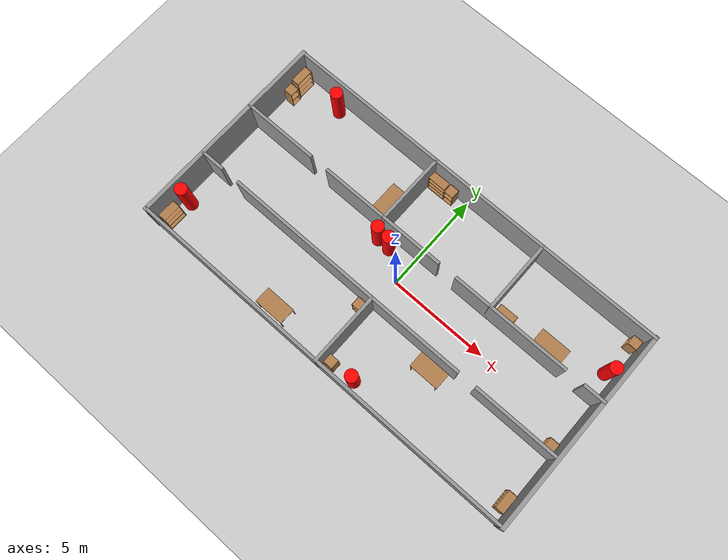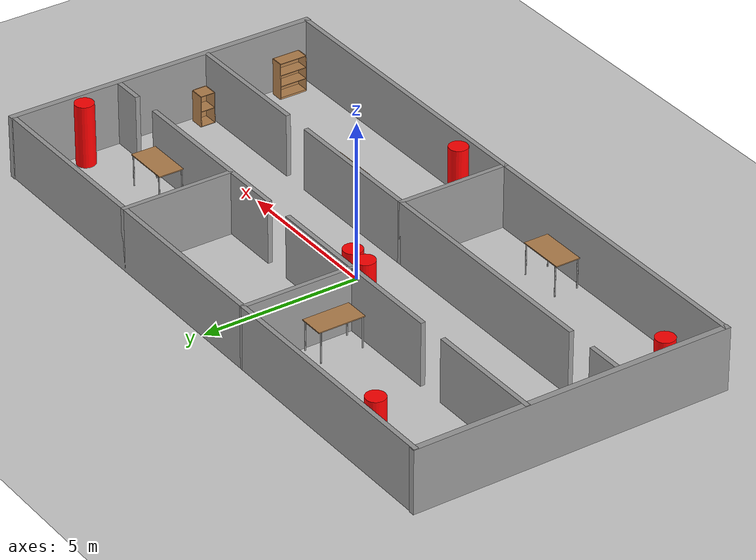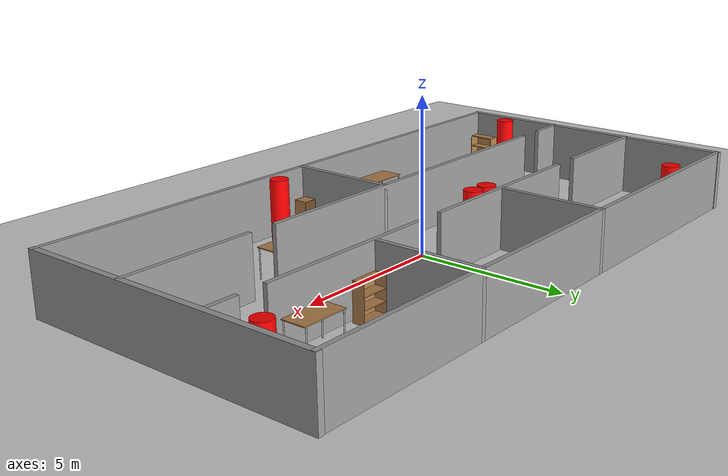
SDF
<sdf version="1.6">
 <world name="default">
  <light name="sun" type="directional">
   <pose>0 0 10 0 -0 0</pose>
   <diffuse>0.8 0.8 0.8 1</diffuse>
   <specular>0.2 0.2 0.2 1</specular>
   <attenuation>
    <range>1000</range>
    <constant>0.9</constant>
    <linear>0.01</linear>
    <quadratic>0.001</quadratic>
   </attenuation>
   <direction>-0.5 0.1 -0.9</direction>
  </light>
  <model name="ground_plane">
   <static>1</static>
   <link name="link">
    <collision name="collision">
     <geometry><plane><normal>0 0 1</normal><size>100 100</size></plane></geometry>
     <surface>
      <contact><collide_bitmask>65535</collide_bitmask></contact>
      <friction><ode><mu>100</mu><mu2>50</mu2></ode></friction>
     </surface>
    </collision>
    <visual name="visual">
     <cast_shadows>0</cast_shadows>
     <geometry><plane><normal>0 0 1</normal><size>100 100</size></plane></geometry>
     <material>
      <script><uri>file://media/materials/scripts/gazebo.material</uri><name>Gazebo/Grey</name></script>
     </material>
    </visual>
   </link>
  </model>
  <gravity>0 0 -9.8</gravity>
  <magnetic_field>6e-06 2.3e-05 -4.2e-05</magnetic_field>
  <atmosphere type="adiabatic"/>
  <physics name="default_physics" default="0" type="ode">
   <max_step_size>0.001</max_step_size>
   <real_time_factor>1</real_time_factor>
   <real_time_update_rate>1000</real_time_update_rate>
  </physics>
  <scene><ambient>0.4 0.4 0.4 1</ambient><background>0.7 0.7 0.7 1</background><shadows>1</shadows></scene>
  <audio><device>default</device></audio>
  <spherical_coordinates>
   <surface_model>EARTH_WGS84</surface_model>
   <latitude_deg>0</latitude_deg>
   <longitude_deg>0</longitude_deg>
   <elevation>0</elevation>
   <heading_deg>0</heading_deg>
  </spherical_coordinates>
  <model name="indoor1">
   <link name="Wall_17">
    <pose>0 -1.5 0 0 -0 0</pose>
    <visual name="Wall_17_Visual_0">
     <pose>-9.43386 0 1 0 -0 0</pose>
     <geometry><box><size>1.28227 0.15 2</size></box></geometry>
     <material>
      <script><uri>file://media/materials/scripts/gazebo.material</uri><name>Gazebo/Grey</name></script>
      <ambient>1 1 1 1</ambient>
     </material>
     <meta><layer>0</layer></meta>
    </visual>
    <collision name="Wall_17_Collision_0">
     <geometry><box><size>1.28227 0.15 2</size></box></geometry>
     <pose>-9.43386 0 1 0 -0 0</pose>
    </collision>
    <visual name="Wall_17_Visual_1">
     <pose>-1.56699 0 1 0 -0 0</pose>
     <geometry><box><size>12.6515 0.15 2</size></box></geometry>
     <material>
      <script><uri>file://media/materials/scripts/gazebo.material</uri><name>Gazebo/Grey</name></script>
      <ambient>1 1 1 1</ambient>
     </material>
     <meta><layer>0</layer></meta>
    </visual>
    <collision name="Wall_17_Collision_1">
     <geometry><box><size>12.6515 0.15 2</size></box></geometry>
     <pose>-1.56699 0 1 0 -0 0</pose>
    </collision>
    <visual name="Wall_17_Visual_2">
     <pose>7.86687 0 1 0 -0 0</pose>
     <geometry><box><size>4.41625 0.15 2</size></box></geometry>
     <material>
      <script><uri>file://media/materials/scripts/gazebo.material</uri><name>Gazebo/Grey</name></script>
      <ambient>1 1 1 1</ambient>
     </material>
     <meta><layer>0</layer></meta>
    </visual>
    <collision name="Wall_17_Collision_2">
     <geometry><box><size>4.41625 0.15 2</size></box></geometry>
     <pose>7.86687 0 1 0 -0 0</pose>
    </collision>
   </link>
   <link name="Wall_19">
    <pose>0 1.5 0 0 -0 0</pose>
    <visual name="Wall_19_Visual_0">
     <pose>-8.16437 0 1 0 -0 0</pose>
     <geometry><box><size>3.82126 0.15 2</size></box></geometry>
     <material>
      <script><uri>file://media/materials/scripts/gazebo.material</uri><name>Gazebo/Grey</name></script>
      <ambient>1 1 1 1</ambient>
     </material>
     <meta><layer>0</layer></meta>
    </visual>
    <collision name="Wall_19_Collision_0">
     <geometry><box><size>3.82126 0.15 2</size></box></geometry>
     <pose>-8.16437 0 1 0 -0 0</pose>
    </collision>
    <visual name="Wall_19_Visual_1">
     <pose>-2.10232 0 1 0 -0 0</pose>
     <geometry><box><size>6.50284 0.15 2</size></box></geometry>
     <material>
      <script><uri>file://media/materials/scripts/gazebo.material</uri><name>Gazebo/Grey</name></script>
      <ambient>1 1 1 1</ambient>
     </material>
     <meta><layer>0</layer></meta>
    </visual>
    <collision name="Wall_19_Collision_1">
     <geometry><box><size>6.50284 0.15 2</size></box></geometry>
     <pose>-2.10232 0 1 0 -0 0</pose>
    </collision>
    <visual name="Wall_19_Visual_2">
     <pose>5.0405 0 1 0 -0 0</pose>
     <geometry><box><size>5.9828 0.15 2</size></box></geometry>
     <material>
      <script><uri>file://media/materials/scripts/gazebo.material</uri><name>Gazebo/Grey</name></script>
      <ambient>1 1 1 1</ambient>
     </material>
     <meta><layer>0</layer></meta>
    </visual>
    <collision name="Wall_19_Collision_2">
     <geometry><box><size>5.9828 0.15 2</size></box></geometry>
     <pose>5.0405 0 1 0 -0 0</pose>
    </collision>
    <visual name="Wall_19_Visual_3">
     <pose>9.50345 0 1 0 -0 0</pose>
     <geometry><box><size>1.1431 0.15 2</size></box></geometry>
     <material>
      <script><uri>file://media/materials/scripts/gazebo.material</uri><name>Gazebo/Grey</name></script>
      <ambient>1 1 1 1</ambient>
     </material>
     <meta><layer>0</layer></meta>
    </visual>
    <collision name="Wall_19_Collision_3">
     <geometry><box><size>1.1431 0.15 2</size></box></geometry>
     <pose>9.50345 0 1 0 -0 0</pose>
    </collision>
   </link>
   <link name="Wall_21">
    <collision name="Wall_21_Collision">
     <geometry><box><size>3.65 0.15 2</size></box></geometry>
     <pose>0 0 1 0 -0 0</pose>
    </collision>
    <visual name="Wall_21_Visual">
     <pose>0 0 1 0 -0 0</pose>
     <geometry><box><size>3.65 0.15 2</size></box></geometry>
     <material>
      <script><uri>file://media/materials/scripts/gazebo.material</uri><name>Gazebo/Grey</name></script>
      <ambient>1 1 1 1</ambient>
     </material>
     <meta><layer>0</layer></meta>
    </visual>
    <pose>-2 3.25 0 0 -0 1.5708</pose>
   </link>
   <link name="Wall_23">
    <collision name="Wall_23_Collision">
     <geometry><box><size>3.65 0.15 2</size></box></geometry>
     <pose>0 0 1 0 -0 0</pose>
    </collision>
    <visual name="Wall_23_Visual">
     <pose>0 0 1 0 -0 0</pose>
     <geometry><box><size>3.65 0.15 2</size></box></geometry>
     <material>
      <script><uri>file://media/materials/scripts/gazebo.material</uri><name>Gazebo/Grey</name></script>
      <ambient>1 1 1 1</ambient>
     </material>
     <meta><layer>0</layer></meta>
    </visual>
    <pose>4 3.25 0 0 -0 1.5708</pose>
   </link>
   <link name="Wall_25">
    <collision name="Wall_25_Collision">
     <geometry><box><size>3.65 0.15 2</size></box></geometry>
     <pose>0 0 1 0 -0 0</pose>
    </collision>
    <visual name="Wall_25_Visual">
     <pose>0 0 1 0 -0 0</pose>
     <geometry><box><size>3.65 0.15 2</size></box></geometry>
     <material>
      <script><uri>file://media/materials/scripts/gazebo.material</uri><name>Gazebo/Grey</name></script>
      <ambient>1 1 1 1</ambient>
     </material>
     <meta><layer>0</layer></meta>
    </visual>
    <pose>0 -3.25 0 0 -0 1.5708</pose>
   </link>
   <link name="Wall_5">
    <collision name="Wall_5_Collision">
     <geometry><box><size>20.15 0.15 2</size></box></geometry>
     <pose>0 0 1 0 -0 0</pose>
    </collision>
    <visual name="Wall_5_Visual">
     <pose>0 0 1 0 -0 0</pose>
     <geometry><box><size>20.15 0.15 2</size></box></geometry>
     <material>
      <script><uri>file://media/materials/scripts/gazebo.material</uri><name>Gazebo/Grey</name></script>
      <ambient>1 1 1 1</ambient>
     </material>
     <meta><layer>0</layer></meta>
    </visual>
    <pose>0 5 0 0 -0 0</pose>
   </link>
   <link name="Wall_6">
    <collision name="Wall_6_Collision">
     <geometry><box><size>10.2 0.2 2</size></box></geometry>
     <pose>0 0 1 0 -0 0</pose>
    </collision>
    <visual name="Wall_6_Visual">
     <pose>0 0 1 0 -0 0</pose>
     <geometry><box><size>10.2 0.2 2</size></box></geometry>
     <material>
      <script><uri>file://media/materials/scripts/gazebo.material</uri><name>Gazebo/Grey</name></script>
      <ambient>1 1 1 1</ambient>
     </material>
     <meta><layer>0</layer></meta>
    </visual>
    <pose>10 0 0 0 0 -1.5708</pose>
   </link>
   <link name="Wall_7">
    <collision name="Wall_7_Collision">
     <geometry><box><size>20.15 0.15 2</size></box></geometry>
     <pose>0 0 1 0 -0 0</pose>
    </collision>
    <visual name="Wall_7_Visual">
     <pose>0 0 1 0 -0 0</pose>
     <geometry><box><size>20.15 0.15 2</size></box></geometry>
     <material>
      <script><uri>file://media/materials/scripts/gazebo.material</uri><name>Gazebo/Grey</name></script>
      <ambient>1 1 1 1</ambient>
     </material>
     <meta><layer>0</layer></meta>
    </visual>
    <pose>0 -5 0 0 -0 3.14159</pose>
   </link>
   <link name="Wall_8">
    <collision name="Wall_8_Collision">
     <geometry><box><size>10.2 0.2 2</size></box></geometry>
     <pose>0 0 1 0 -0 0</pose>
    </collision>
    <visual name="Wall_8_Visual">
     <pose>0 0 1 0 -0 0</pose>
     <geometry><box><size>10.2 0.2 2</size></box></geometry>
     <material>
      <script><uri>file://media/materials/scripts/gazebo.material</uri><name>Gazebo/Grey</name></script>
      <ambient>1 1 1 1</ambient>
     </material>
     <meta><layer>0</layer></meta>
    </visual>
    <pose>-10 0 0 0 -0 1.5708</pose>
   </link>
   <static>1</static>
  </model>
  <model name="bookshelf">
   <static>1</static>
   <link name="link">
    <inertial><mass>1</mass></inertial>
    <collision name="back">
     <pose>0 0.005 0.6 0 -0 0</pose>
     <geometry><box><size>0.9 0.01 1.2</size></box></geometry>
    </collision>
    <visual name="visual1">
     <pose>0 0.005 0.6 0 -0 0</pose>
     <geometry><box><size>0.9 0.01 1.2</size></box></geometry>
     <material>
      <script><uri>file://media/materials/scripts/gazebo.material</uri><name>Gazebo/Wood</name></script>
     </material>
    </visual>
    <collision name="left_side">
     <pose>0.45 -0.195 0.6 0 -0 0</pose>
     <geometry><box><size>0.02 0.4 1.2</size></box></geometry>
    </collision>
    <visual name="visual2">
     <pose>0.45 -0.195 0.6 0 -0 0</pose>
     <geometry><box><size>0.02 0.4 1.2</size></box></geometry>
     <material>
      <script><uri>file://media/materials/scripts/gazebo.material</uri><name>Gazebo/Wood</name></script>
     </material>
    </visual>
    <collision name="right_side">
     <pose>-0.45 -0.195 0.6 0 -0 0</pose>
     <geometry><box><size>0.02 0.4 1.2</size></box></geometry>
    </collision>
    <visual name="visual3">
     <pose>-0.45 -0.195 0.6 0 -0 0</pose>
     <geometry><box><size>0.02 0.4 1.2</size></box></geometry>
     <material>
      <script><uri>file://media/materials/scripts/gazebo.material</uri><name>Gazebo/Wood</name></script>
     </material>
    </visual>
    <collision name="bottom">
     <pose>0 -0.195 0.03 0 -0 0</pose>
     <geometry><box><size>0.88 0.4 0.06</size></box></geometry>
    </collision>
    <visual name="visual4">
     <pose>0 -0.195 0.03 0 -0 0</pose>
     <geometry><box><size>0.88 0.4 0.06</size></box></geometry>
     <material>
      <script><uri>file://media/materials/scripts/gazebo.material</uri><name>Gazebo/Wood</name></script>
     </material>
    </visual>
    <collision name="top">
     <pose>0 -0.195 1.19 0 -0 0</pose>
     <geometry><box><size>0.88 0.4 0.02</size></box></geometry>
    </collision>
    <visual name="visual5">
     <pose>0 -0.195 1.19 0 -0 0</pose>
     <geometry><box><size>0.88 0.4 0.02</size></box></geometry>
     <material>
      <script><uri>file://media/materials/scripts/gazebo.material</uri><name>Gazebo/Wood</name></script>
     </material>
    </visual>
    <collision name="low_shelf">
     <pose>0 -0.195 0.43 0 -0 0</pose>
     <geometry><box><size>0.88 0.4 0.02</size></box></geometry>
    </collision>
    <visual name="visual6">
     <pose>0 -0.195 0.43 0 -0 0</pose>
     <geometry><box><size>0.88 0.4 0.02</size></box></geometry>
     <material>
      <script><uri>file://media/materials/scripts/gazebo.material</uri><name>Gazebo/Wood</name></script>
     </material>
    </visual>
    <collision name="high_shelf">
     <pose>0 -0.195 0.8 0 -0 0</pose>
     <geometry><box><size>0.88 0.4 0.02</size></box></geometry>
    </collision>
    <visual name="visual7">
     <pose>0 -0.195 0.8 0 -0 0</pose>
     <geometry><box><size>0.88 0.4 0.02</size></box></geometry>
     <material>
      <script><uri>file://media/materials/scripts/gazebo.material</uri><name>Gazebo/Wood</name></script>
     </material>
    </visual>
   </link>
   <pose>-9.72657 -4.37218 0 0 -0 1.5708</pose>
  </model>
  <model name="bookshelf_clone">
   <static>1</static>
   <link name="link">
    <inertial><mass>1</mass></inertial>
    <collision name="back">
     <pose>0 0.005 0.6 0 -0 0</pose>
     <geometry><box><size>0.9 0.01 1.2</size></box></geometry>
    </collision>
    <visual name="visual1">
     <pose>0 0.005 0.6 0 -0 0</pose>
     <geometry><box><size>0.9 0.01 1.2</size></box></geometry>
     <material>
      <script><uri>file://media/materials/scripts/gazebo.material</uri><name>Gazebo/Wood</name></script>
     </material>
    </visual>
    <collision name="left_side">
     <pose>0.45 -0.195 0.6 0 -0 0</pose>
     <geometry><box><size>0.02 0.4 1.2</size></box></geometry>
    </collision>
    <visual name="visual2">
     <pose>0.45 -0.195 0.6 0 -0 0</pose>
     <geometry><box><size>0.02 0.4 1.2</size></box></geometry>
     <material>
      <script><uri>file://media/materials/scripts/gazebo.material</uri><name>Gazebo/Wood</name></script>
     </material>
    </visual>
    <collision name="right_side">
     <pose>-0.45 -0.195 0.6 0 -0 0</pose>
     <geometry><box><size>0.02 0.4 1.2</size></box></geometry>
    </collision>
    <visual name="visual3">
     <pose>-0.45 -0.195 0.6 0 -0 0</pose>
     <geometry><box><size>0.02 0.4 1.2</size></box></geometry>
     <material>
      <script><uri>file://media/materials/scripts/gazebo.material</uri><name>Gazebo/Wood</name></script>
     </material>
    </visual>
    <collision name="bottom">
     <pose>0 -0.195 0.03 0 -0 0</pose>
     <geometry><box><size>0.88 0.4 0.06</size></box></geometry>
    </collision>
    <visual name="visual4">
     <pose>0 -0.195 0.03 0 -0 0</pose>
     <geometry><box><size>0.88 0.4 0.06</size></box></geometry>
     <material>
      <script><uri>file://media/materials/scripts/gazebo.material</uri><name>Gazebo/Wood</name></script>
     </material>
    </visual>
    <collision name="top">
     <pose>0 -0.195 1.19 0 -0 0</pose>
     <geometry><box><size>0.88 0.4 0.02</size></box></geometry>
    </collision>
    <visual name="visual5">
     <pose>0 -0.195 1.19 0 -0 0</pose>
     <geometry><box><size>0.88 0.4 0.02</size></box></geometry>
     <material>
      <script><uri>file://media/materials/scripts/gazebo.material</uri><name>Gazebo/Wood</name></script>
     </material>
    </visual>
    <collision name="low_shelf">
     <pose>0 -0.195 0.43 0 -0 0</pose>
     <geometry><box><size>0.88 0.4 0.02</size></box></geometry>
    </collision>
    <visual name="visual6">
     <pose>0 -0.195 0.43 0 -0 0</pose>
     <geometry><box><size>0.88 0.4 0.02</size></box></geometry>
     <material>
      <script><uri>file://media/materials/scripts/gazebo.material</uri><name>Gazebo/Wood</name></script>
     </material>
    </visual>
    <collision name="high_shelf">
     <pose>0 -0.195 0.8 0 -0 0</pose>
     <geometry><box><size>0.88 0.4 0.02</size></box></geometry>
    </collision>
    <visual name="visual7">
     <pose>0 -0.195 0.8 0 -0 0</pose>
     <geometry><box><size>0.88 0.4 0.02</size></box></geometry>
     <material>
      <script><uri>file://media/materials/scripts/gazebo.material</uri><name>Gazebo/Wood</name></script>
     </material>
    </visual>
   </link>
   <pose>-1.44327 4.80493 0 0 -0 4e-06</pose>
  </model>
  <model name="bookshelf_clone_0">
   <static>1</static>
   <link name="link">
    <inertial><mass>1</mass></inertial>
    <collision name="back">
     <pose>0 0.005 0.6 0 -0 0</pose>
     <geometry><box><size>0.9 0.01 1.2</size></box></geometry>
    </collision>
    <visual name="visual1">
     <pose>0 0.005 0.6 0 -0 0</pose>
     <geometry><box><size>0.9 0.01 1.2</size></box></geometry>
     <material>
      <script><uri>file://media/materials/scripts/gazebo.material</uri><name>Gazebo/Wood</name></script>
     </material>
    </visual>
    <collision name="left_side">
     <pose>0.45 -0.195 0.6 0 -0 0</pose>
     <geometry><box><size>0.02 0.4 1.2</size></box></geometry>
    </collision>
    <visual name="visual2">
     <pose>0.45 -0.195 0.6 0 -0 0</pose>
     <geometry><box><size>0.02 0.4 1.2</size></box></geometry>
     <material>
      <script><uri>file://media/materials/scripts/gazebo.material</uri><name>Gazebo/Wood</name></script>
     </material>
    </visual>
    <collision name="right_side">
     <pose>-0.45 -0.195 0.6 0 -0 0</pose>
     <geometry><box><size>0.02 0.4 1.2</size></box></geometry>
    </collision>
    <visual name="visual3">
     <pose>-0.45 -0.195 0.6 0 -0 0</pose>
     <geometry><box><size>0.02 0.4 1.2</size></box></geometry>
     <material>
      <script><uri>file://media/materials/scripts/gazebo.material</uri><name>Gazebo/Wood</name></script>
     </material>
    </visual>
    <collision name="bottom">
     <pose>0 -0.195 0.03 0 -0 0</pose>
     <geometry><box><size>0.88 0.4 0.06</size></box></geometry>
    </collision>
    <visual name="visual4">
     <pose>0 -0.195 0.03 0 -0 0</pose>
     <geometry><box><size>0.88 0.4 0.06</size></box></geometry>
     <material>
      <script><uri>file://media/materials/scripts/gazebo.material</uri><name>Gazebo/Wood</name></script>
     </material>
    </visual>
    <collision name="top">
     <pose>0 -0.195 1.19 0 -0 0</pose>
     <geometry><box><size>0.88 0.4 0.02</size></box></geometry>
    </collision>
    <visual name="visual5">
     <pose>0 -0.195 1.19 0 -0 0</pose>
     <geometry><box><size>0.88 0.4 0.02</size></box></geometry>
     <material>
      <script><uri>file://media/materials/scripts/gazebo.material</uri><name>Gazebo/Wood</name></script>
     </material>
    </visual>
    <collision name="low_shelf">
     <pose>0 -0.195 0.43 0 -0 0</pose>
     <geometry><box><size>0.88 0.4 0.02</size></box></geometry>
    </collision>
    <visual name="visual6">
     <pose>0 -0.195 0.43 0 -0 0</pose>
     <geometry><box><size>0.88 0.4 0.02</size></box></geometry>
     <material>
      <script><uri>file://media/materials/scripts/gazebo.material</uri><name>Gazebo/Wood</name></script>
     </material>
    </visual>
    <collision name="high_shelf">
     <pose>0 -0.195 0.8 0 -0 0</pose>
     <geometry><box><size>0.88 0.4 0.02</size></box></geometry>
    </collision>
    <visual name="visual7">
     <pose>0 -0.195 0.8 0 -0 0</pose>
     <geometry><box><size>0.88 0.4 0.02</size></box></geometry>
     <material>
      <script><uri>file://media/materials/scripts/gazebo.material</uri><name>Gazebo/Wood</name></script>
     </material>
    </visual>
   </link>
   <pose>4.67727 1.69299 0 0 0 -3.14159</pose>
  </model>
  <model name="bookshelf_clone_1">
   <static>1</static>
   <link name="link">
    <inertial><mass>1</mass></inertial>
    <collision name="back">
     <pose>0 0.005 0.6 0 -0 0</pose>
     <geometry><box><size>0.9 0.01 1.2</size></box></geometry>
    </collision>
    <visual name="visual1">
     <pose>0 0.005 0.6 0 -0 0</pose>
     <geometry><box><size>0.9 0.01 1.2</size></box></geometry>
     <material>
      <script><uri>file://media/materials/scripts/gazebo.material</uri><name>Gazebo/Wood</name></script>
     </material>
    </visual>
    <collision name="left_side">
     <pose>0.45 -0.195 0.6 0 -0 0</pose>
     <geometry><box><size>0.02 0.4 1.2</size></box></geometry>
    </collision>
    <visual name="visual2">
     <pose>0.45 -0.195 0.6 0 -0 0</pose>
     <geometry><box><size>0.02 0.4 1.2</size></box></geometry>
     <material>
      <script><uri>file://media/materials/scripts/gazebo.material</uri><name>Gazebo/Wood</name></script>
     </material>
    </visual>
    <collision name="right_side">
     <pose>-0.45 -0.195 0.6 0 -0 0</pose>
     <geometry><box><size>0.02 0.4 1.2</size></box></geometry>
    </collision>
    <visual name="visual3">
     <pose>-0.45 -0.195 0.6 0 -0 0</pose>
     <geometry><box><size>0.02 0.4 1.2</size></box></geometry>
     <material>
      <script><uri>file://media/materials/scripts/gazebo.material</uri><name>Gazebo/Wood</name></script>
     </material>
    </visual>
    <collision name="bottom">
     <pose>0 -0.195 0.03 0 -0 0</pose>
     <geometry><box><size>0.88 0.4 0.06</size></box></geometry>
    </collision>
    <visual name="visual4">
     <pose>0 -0.195 0.03 0 -0 0</pose>
     <geometry><box><size>0.88 0.4 0.06</size></box></geometry>
     <material>
      <script><uri>file://media/materials/scripts/gazebo.material</uri><name>Gazebo/Wood</name></script>
     </material>
    </visual>
    <collision name="top">
     <pose>0 -0.195 1.19 0 -0 0</pose>
     <geometry><box><size>0.88 0.4 0.02</size></box></geometry>
    </collision>
    <visual name="visual5">
     <pose>0 -0.195 1.19 0 -0 0</pose>
     <geometry><box><size>0.88 0.4 0.02</size></box></geometry>
     <material>
      <script><uri>file://media/materials/scripts/gazebo.material</uri><name>Gazebo/Wood</name></script>
     </material>
    </visual>
    <collision name="low_shelf">
     <pose>0 -0.195 0.43 0 -0 0</pose>
     <geometry><box><size>0.88 0.4 0.02</size></box></geometry>
    </collision>
    <visual name="visual6">
     <pose>0 -0.195 0.43 0 -0 0</pose>
     <geometry><box><size>0.88 0.4 0.02</size></box></geometry>
     <material>
      <script><uri>file://media/materials/scripts/gazebo.material</uri><name>Gazebo/Wood</name></script>
     </material>
    </visual>
    <collision name="high_shelf">
     <pose>0 -0.195 0.8 0 -0 0</pose>
     <geometry><box><size>0.88 0.4 0.02</size></box></geometry>
    </collision>
    <visual name="visual7">
     <pose>0 -0.195 0.8 0 -0 0</pose>
     <geometry><box><size>0.88 0.4 0.02</size></box></geometry>
     <material>
      <script><uri>file://media/materials/scripts/gazebo.material</uri><name>Gazebo/Wood</name></script>
     </material>
    </visual>
   </link>
   <pose>9.76318 -4.11921 0 0 0 -1.57079</pose>
  </model>
  <model name="bookshelf_clone_2">
   <static>1</static>
   <link name="link">
    <inertial><mass>1</mass></inertial>
    <collision name="back">
     <pose>0 0.005 0.6 0 -0 0</pose>
     <geometry><box><size>0.9 0.01 1.2</size></box></geometry>
    </collision>
    <visual name="visual1">
     <pose>0 0.005 0.6 0 -0 0</pose>
     <geometry><box><size>0.9 0.01 1.2</size></box></geometry>
     <material>
      <script><uri>file://media/materials/scripts/gazebo.material</uri><name>Gazebo/Wood</name></script>
     </material>
    </visual>
    <collision name="left_side">
     <pose>0.45 -0.195 0.6 0 -0 0</pose>
     <geometry><box><size>0.02 0.4 1.2</size></box></geometry>
    </collision>
    <visual name="visual2">
     <pose>0.45 -0.195 0.6 0 -0 0</pose>
     <geometry><box><size>0.02 0.4 1.2</size></box></geometry>
     <material>
      <script><uri>file://media/materials/scripts/gazebo.material</uri><name>Gazebo/Wood</name></script>
     </material>
    </visual>
    <collision name="right_side">
     <pose>-0.45 -0.195 0.6 0 -0 0</pose>
     <geometry><box><size>0.02 0.4 1.2</size></box></geometry>
    </collision>
    <visual name="visual3">
     <pose>-0.45 -0.195 0.6 0 -0 0</pose>
     <geometry><box><size>0.02 0.4 1.2</size></box></geometry>
     <material>
      <script><uri>file://media/materials/scripts/gazebo.material</uri><name>Gazebo/Wood</name></script>
     </material>
    </visual>
    <collision name="bottom">
     <pose>0 -0.195 0.03 0 -0 0</pose>
     <geometry><box><size>0.88 0.4 0.06</size></box></geometry>
    </collision>
    <visual name="visual4">
     <pose>0 -0.195 0.03 0 -0 0</pose>
     <geometry><box><size>0.88 0.4 0.06</size></box></geometry>
     <material>
      <script><uri>file://media/materials/scripts/gazebo.material</uri><name>Gazebo/Wood</name></script>
     </material>
    </visual>
    <collision name="top">
     <pose>0 -0.195 1.19 0 -0 0</pose>
     <geometry><box><size>0.88 0.4 0.02</size></box></geometry>
    </collision>
    <visual name="visual5">
     <pose>0 -0.195 1.19 0 -0 0</pose>
     <geometry><box><size>0.88 0.4 0.02</size></box></geometry>
     <material>
      <script><uri>file://media/materials/scripts/gazebo.material</uri><name>Gazebo/Wood</name></script>
     </material>
    </visual>
    <collision name="low_shelf">
     <pose>0 -0.195 0.43 0 -0 0</pose>
     <geometry><box><size>0.88 0.4 0.02</size></box></geometry>
    </collision>
    <visual name="visual6">
     <pose>0 -0.195 0.43 0 -0 0</pose>
     <geometry><box><size>0.88 0.4 0.02</size></box></geometry>
     <material>
      <script><uri>file://media/materials/scripts/gazebo.material</uri><name>Gazebo/Wood</name></script>
     </material>
    </visual>
    <collision name="high_shelf">
     <pose>0 -0.195 0.8 0 -0 0</pose>
     <geometry><box><size>0.88 0.4 0.02</size></box></geometry>
    </collision>
    <visual name="visual7">
     <pose>0 -0.195 0.8 0 -0 0</pose>
     <geometry><box><size>0.88 0.4 0.02</size></box></geometry>
     <material>
      <script><uri>file://media/materials/scripts/gazebo.material</uri><name>Gazebo/Wood</name></script>
     </material>
    </visual>
   </link>
   <pose>-9.82487 4.34326 0 0 -0 1.5708</pose>
  </model>
  <model name="cabinet">
   <static>1</static>
   <link name="cabinet_bottom_plate">
    <inertial>
     <pose>0 0 -1 0 -0 0</pose>
     <inertia><ixx>2.05</ixx><ixy>0</ixy><ixz>0</ixz><iyy>2.05</iyy><iyz>0</iyz><izz>2.05</izz></inertia>
     <mass>25</mass>
    </inertial>
    <collision name="cabinet_bottom_plate_geom">
     <pose>0 0 0.01 0 -0 0</pose>
     <geometry><box><size>0.45 0.45 0.02</size></box></geometry>
    </collision>
    <visual name="cabinet_bottom_plate_geom_visual">
     <pose>0 0 0.01 0 -0 0</pose>
     <geometry><box><size>0.45 0.45 0.02</size></box></geometry>
     <material>
      <script><uri>file://media/materials/scripts/gazebo.material</uri><name>Gazebo/Wood</name></script>
     </material>
    </visual>
    <collision name="cabinet_bottom_plate_geom_cabinet_back_plate">
     <pose>0.235 0 0.51 0 -0 0</pose>
     <geometry><box><size>0.02 0.45 1.02</size></box></geometry>
    </collision>
    <visual name="cabinet_bottom_plate_geom_cabinet_back_plate_visual">
     <pose>0.235 0 0.51 0 -0 0</pose>
     <geometry><box><size>0.02 0.45 1.02</size></box></geometry>
     <material>
      <script><uri>file://media/materials/scripts/gazebo.material</uri><name>Gazebo/Wood</name></script>
     </material>
    </visual>
    <collision name="cabinet_bottom_plate_geom_cabinet_left_plate">
     <pose>0 0.235 0.51 0 -0 0</pose>
     <geometry><box><size>0.45 0.02 1.02</size></box></geometry>
    </collision>
    <visual name="cabinet_bottom_plate_geom_cabinet_left_plate_visual">
     <pose>0 0.235 0.51 0 -0 0</pose>
     <geometry><box><size>0.45 0.02 1.02</size></box></geometry>
     <material>
      <script><uri>file://media/materials/scripts/gazebo.material</uri><name>Gazebo/Wood</name></script>
     </material>
    </visual>
    <collision name="cabinet_bottom_plate_geom_cabinet_middle_plate">
     <pose>0 0 0.51 0 -0 0</pose>
     <geometry><box><size>0.45 0.45 0.02</size></box></geometry>
    </collision>
    <visual name="cabinet_bottom_plate_geom_cabinet_middle_plate_visual">
     <pose>0 0 0.51 0 -0 0</pose>
     <geometry><box><size>0.45 0.45 0.02</size></box></geometry>
     <material>
      <script><uri>file://media/materials/scripts/gazebo.material</uri><name>Gazebo/Wood</name></script>
     </material>
    </visual>
    <collision name="cabinet_bottom_plate_geom_cabinet_right_plate">
     <pose>0 -0.235 0.51 0 -0 0</pose>
     <geometry><box><size>0.45 0.02 1.02</size></box></geometry>
    </collision>
    <visual name="cabinet_bottom_plate_geom_cabinet_right_plate_visual">
     <pose>0 -0.235 0.51 0 -0 0</pose>
     <geometry><box><size>0.45 0.02 1.02</size></box></geometry>
     <material>
      <script><uri>file://media/materials/scripts/gazebo.material</uri><name>Gazebo/Wood</name></script>
     </material>
    </visual>
    <collision name="cabinet_bottom_plate_geom_cabinet_top_plate">
     <pose>0 0 1.01 0 -0 0</pose>
     <geometry><box><size>0.45 0.45 0.02</size></box></geometry>
    </collision>
    <visual name="cabinet_bottom_plate_geom_cabinet_top_plate_visual">
     <pose>0 0 1.01 0 -0 0</pose>
     <geometry><box><size>0.45 0.45 0.02</size></box></geometry>
     <material>
      <script><uri>file://media/materials/scripts/gazebo.material</uri><name>Gazebo/Wood</name></script>
     </material>
    </visual>
   </link>
   <pose>9.58424 4.59301 0 0 -0 0</pose>
  </model>
  <model name="cabinet_clone">
   <static>1</static>
   <link name="cabinet_bottom_plate">
    <inertial>
     <pose>0 0 -1 0 -0 0</pose>
     <inertia><ixx>2.05</ixx><ixy>0</ixy><ixz>0</ixz><iyy>2.05</iyy><iyz>0</iyz><izz>2.05</izz></inertia>
     <mass>25</mass>
    </inertial>
    <collision name="cabinet_bottom_plate_geom">
     <pose>0 0 0.01 0 -0 0</pose>
     <geometry><box><size>0.45 0.45 0.02</size></box></geometry>
    </collision>
    <visual name="cabinet_bottom_plate_geom_visual">
     <pose>0 0 0.01 0 -0 0</pose>
     <geometry><box><size>0.45 0.45 0.02</size></box></geometry>
     <material>
      <script><uri>file://media/materials/scripts/gazebo.material</uri><name>Gazebo/Wood</name></script>
     </material>
    </visual>
    <collision name="cabinet_bottom_plate_geom_cabinet_back_plate">
     <pose>0.235 0 0.51 0 -0 0</pose>
     <geometry><box><size>0.02 0.45 1.02</size></box></geometry>
    </collision>
    <visual name="cabinet_bottom_plate_geom_cabinet_back_plate_visual">
     <pose>0.235 0 0.51 0 -0 0</pose>
     <geometry><box><size>0.02 0.45 1.02</size></box></geometry>
     <material>
      <script><uri>file://media/materials/scripts/gazebo.material</uri><name>Gazebo/Wood</name></script>
     </material>
    </visual>
    <collision name="cabinet_bottom_plate_geom_cabinet_left_plate">
     <pose>0 0.235 0.51 0 -0 0</pose>
     <geometry><box><size>0.45 0.02 1.02</size></box></geometry>
    </collision>
    <visual name="cabinet_bottom_plate_geom_cabinet_left_plate_visual">
     <pose>0 0.235 0.51 0 -0 0</pose>
     <geometry><box><size>0.45 0.02 1.02</size></box></geometry>
     <material>
      <script><uri>file://media/materials/scripts/gazebo.material</uri><name>Gazebo/Wood</name></script>
     </material>
    </visual>
    <collision name="cabinet_bottom_plate_geom_cabinet_middle_plate">
     <pose>0 0 0.51 0 -0 0</pose>
     <geometry><box><size>0.45 0.45 0.02</size></box></geometry>
    </collision>
    <visual name="cabinet_bottom_plate_geom_cabinet_middle_plate_visual">
     <pose>0 0 0.51 0 -0 0</pose>
     <geometry><box><size>0.45 0.45 0.02</size></box></geometry>
     <material>
      <script><uri>file://media/materials/scripts/gazebo.material</uri><name>Gazebo/Wood</name></script>
     </material>
    </visual>
    <collision name="cabinet_bottom_plate_geom_cabinet_right_plate">
     <pose>0 -0.235 0.51 0 -0 0</pose>
     <geometry><box><size>0.45 0.02 1.02</size></box></geometry>
    </collision>
    <visual name="cabinet_bottom_plate_geom_cabinet_right_plate_visual">
     <pose>0 -0.235 0.51 0 -0 0</pose>
     <geometry><box><size>0.45 0.02 1.02</size></box></geometry>
     <material>
      <script><uri>file://media/materials/scripts/gazebo.material</uri><name>Gazebo/Wood</name></script>
     </material>
    </visual>
    <collision name="cabinet_bottom_plate_geom_cabinet_top_plate">
     <pose>0 0 1.01 0 -0 0</pose>
     <geometry><box><size>0.45 0.45 0.02</size></box></geometry>
    </collision>
    <visual name="cabinet_bottom_plate_geom_cabinet_top_plate_visual">
     <pose>0 0 1.01 0 -0 0</pose>
     <geometry><box><size>0.45 0.45 0.02</size></box></geometry>
     <material>
      <script><uri>file://media/materials/scripts/gazebo.material</uri><name>Gazebo/Wood</name></script>
     </material>
    </visual>
   </link>
   <pose>9.56465 -1.12003 0 0 -0 0</pose>
  </model>
  <model name="cabinet_clone_0">
   <static>1</static>
   <link name="cabinet_bottom_plate">
    <inertial>
     <pose>0 0 -1 0 -0 0</pose>
     <inertia><ixx>2.05</ixx><ixy>0</ixy><ixz>0</ixz><iyy>2.05</iyy><iyz>0</iyz><izz>2.05</izz></inertia>
     <mass>25</mass>
    </inertial>
    <collision name="cabinet_bottom_plate_geom">
     <pose>0 0 0.01 0 -0 0</pose>
     <geometry><box><size>0.45 0.45 0.02</size></box></geometry>
    </collision>
    <visual name="cabinet_bottom_plate_geom_visual">
     <pose>0 0 0.01 0 -0 0</pose>
     <geometry><box><size>0.45 0.45 0.02</size></box></geometry>
     <material>
      <script><uri>file://media/materials/scripts/gazebo.material</uri><name>Gazebo/Wood</name></script>
     </material>
    </visual>
    <collision name="cabinet_bottom_plate_geom_cabinet_back_plate">
     <pose>0.235 0 0.51 0 -0 0</pose>
     <geometry><box><size>0.02 0.45 1.02</size></box></geometry>
    </collision>
    <visual name="cabinet_bottom_plate_geom_cabinet_back_plate_visual">
     <pose>0.235 0 0.51 0 -0 0</pose>
     <geometry><box><size>0.02 0.45 1.02</size></box></geometry>
     <material>
      <script><uri>file://media/materials/scripts/gazebo.material</uri><name>Gazebo/Wood</name></script>
     </material>
    </visual>
    <collision name="cabinet_bottom_plate_geom_cabinet_left_plate">
     <pose>0 0.235 0.51 0 -0 0</pose>
     <geometry><box><size>0.45 0.02 1.02</size></box></geometry>
    </collision>
    <visual name="cabinet_bottom_plate_geom_cabinet_left_plate_visual">
     <pose>0 0.235 0.51 0 -0 0</pose>
     <geometry><box><size>0.45 0.02 1.02</size></box></geometry>
     <material>
      <script><uri>file://media/materials/scripts/gazebo.material</uri><name>Gazebo/Wood</name></script>
     </material>
    </visual>
    <collision name="cabinet_bottom_plate_geom_cabinet_middle_plate">
     <pose>0 0 0.51 0 -0 0</pose>
     <geometry><box><size>0.45 0.45 0.02</size></box></geometry>
    </collision>
    <visual name="cabinet_bottom_plate_geom_cabinet_middle_plate_visual">
     <pose>0 0 0.51 0 -0 0</pose>
     <geometry><box><size>0.45 0.45 0.02</size></box></geometry>
     <material>
      <script><uri>file://media/materials/scripts/gazebo.material</uri><name>Gazebo/Wood</name></script>
     </material>
    </visual>
    <collision name="cabinet_bottom_plate_geom_cabinet_right_plate">
     <pose>0 -0.235 0.51 0 -0 0</pose>
     <geometry><box><size>0.45 0.02 1.02</size></box></geometry>
    </collision>
    <visual name="cabinet_bottom_plate_geom_cabinet_right_plate_visual">
     <pose>0 -0.235 0.51 0 -0 0</pose>
     <geometry><box><size>0.45 0.02 1.02</size></box></geometry>
     <material>
      <script><uri>file://media/materials/scripts/gazebo.material</uri><name>Gazebo/Wood</name></script>
     </material>
    </visual>
    <collision name="cabinet_bottom_plate_geom_cabinet_top_plate">
     <pose>0 0 1.01 0 -0 0</pose>
     <geometry><box><size>0.45 0.45 0.02</size></box></geometry>
    </collision>
    <visual name="cabinet_bottom_plate_geom_cabinet_top_plate_visual">
     <pose>0 0 1.01 0 -0 0</pose>
     <geometry><box><size>0.45 0.45 0.02</size></box></geometry>
     <material>
      <script><uri>file://media/materials/scripts/gazebo.material</uri><name>Gazebo/Wood</name></script>
     </material>
    </visual>
   </link>
   <pose>-0.396131 -1.93123 0 0 -0 1.5708</pose>
  </model>
  <model name="cabinet_clone_1">
   <static>1</static>
   <link name="cabinet_bottom_plate">
    <inertial>
     <pose>0 0 -1 0 -0 0</pose>
     <inertia><ixx>2.05</ixx><ixy>0</ixy><ixz>0</ixz><iyy>2.05</iyy><iyz>0</iyz><izz>2.05</izz></inertia>
     <mass>25</mass>
    </inertial>
    <collision name="cabinet_bottom_plate_geom">
     <pose>0 0 0.01 0 -0 0</pose>
     <geometry><box><size>0.45 0.45 0.02</size></box></geometry>
    </collision>
    <visual name="cabinet_bottom_plate_geom_visual">
     <pose>0 0 0.01 0 -0 0</pose>
     <geometry><box><size>0.45 0.45 0.02</size></box></geometry>
     <material>
      <script><uri>file://media/materials/scripts/gazebo.material</uri><name>Gazebo/Wood</name></script>
     </material>
    </visual>
    <collision name="cabinet_bottom_plate_geom_cabinet_back_plate">
     <pose>0.235 0 0.51 0 -0 0</pose>
     <geometry><box><size>0.02 0.45 1.02</size></box></geometry>
    </collision>
    <visual name="cabinet_bottom_plate_geom_cabinet_back_plate_visual">
     <pose>0.235 0 0.51 0 -0 0</pose>
     <geometry><box><size>0.02 0.45 1.02</size></box></geometry>
     <material>
      <script><uri>file://media/materials/scripts/gazebo.material</uri><name>Gazebo/Wood</name></script>
     </material>
    </visual>
    <collision name="cabinet_bottom_plate_geom_cabinet_left_plate">
     <pose>0 0.235 0.51 0 -0 0</pose>
     <geometry><box><size>0.45 0.02 1.02</size></box></geometry>
    </collision>
    <visual name="cabinet_bottom_plate_geom_cabinet_left_plate_visual">
     <pose>0 0.235 0.51 0 -0 0</pose>
     <geometry><box><size>0.45 0.02 1.02</size></box></geometry>
     <material>
      <script><uri>file://media/materials/scripts/gazebo.material</uri><name>Gazebo/Wood</name></script>
     </material>
    </visual>
    <collision name="cabinet_bottom_plate_geom_cabinet_middle_plate">
     <pose>0 0 0.51 0 -0 0</pose>
     <geometry><box><size>0.45 0.45 0.02</size></box></geometry>
    </collision>
    <visual name="cabinet_bottom_plate_geom_cabinet_middle_plate_visual">
     <pose>0 0 0.51 0 -0 0</pose>
     <geometry><box><size>0.45 0.45 0.02</size></box></geometry>
     <material>
      <script><uri>file://media/materials/scripts/gazebo.material</uri><name>Gazebo/Wood</name></script>
     </material>
    </visual>
    <collision name="cabinet_bottom_plate_geom_cabinet_right_plate">
     <pose>0 -0.235 0.51 0 -0 0</pose>
     <geometry><box><size>0.45 0.02 1.02</size></box></geometry>
    </collision>
    <visual name="cabinet_bottom_plate_geom_cabinet_right_plate_visual">
     <pose>0 -0.235 0.51 0 -0 0</pose>
     <geometry><box><size>0.45 0.02 1.02</size></box></geometry>
     <material>
      <script><uri>file://media/materials/scripts/gazebo.material</uri><name>Gazebo/Wood</name></script>
     </material>
    </visual>
    <collision name="cabinet_bottom_plate_geom_cabinet_top_plate">
     <pose>0 0 1.01 0 -0 0</pose>
     <geometry><box><size>0.45 0.45 0.02</size></box></geometry>
    </collision>
    <visual name="cabinet_bottom_plate_geom_cabinet_top_plate_visual">
     <pose>0 0 1.01 0 -0 0</pose>
     <geometry><box><size>0.45 0.45 0.02</size></box></geometry>
     <material>
      <script><uri>file://media/materials/scripts/gazebo.material</uri><name>Gazebo/Wood</name></script>
     </material>
    </visual>
   </link>
   <pose>-9.58857 3.57077 0 0 0 -3.14159</pose>
  </model>
  <model name="cabinet_clone_2">
   <static>1</static>
   <link name="cabinet_bottom_plate">
    <inertial>
     <pose>0 0 -1 0 -0 0</pose>
     <inertia><ixx>2.05</ixx><ixy>0</ixy><ixz>0</ixz><iyy>2.05</iyy><iyz>0</iyz><izz>2.05</izz></inertia>
     <mass>25</mass>
    </inertial>
    <collision name="cabinet_bottom_plate_geom">
     <pose>0 0 0.01 0 -0 0</pose>
     <geometry><box><size>0.45 0.45 0.02</size></box></geometry>
    </collision>
    <visual name="cabinet_bottom_plate_geom_visual">
     <pose>0 0 0.01 0 -0 0</pose>
     <geometry><box><size>0.45 0.45 0.02</size></box></geometry>
     <material>
      <script><uri>file://media/materials/scripts/gazebo.material</uri><name>Gazebo/Wood</name></script>
     </material>
    </visual>
    <collision name="cabinet_bottom_plate_geom_cabinet_back_plate">
     <pose>0.235 0 0.51 0 -0 0</pose>
     <geometry><box><size>0.02 0.45 1.02</size></box></geometry>
    </collision>
    <visual name="cabinet_bottom_plate_geom_cabinet_back_plate_visual">
     <pose>0.235 0 0.51 0 -0 0</pose>
     <geometry><box><size>0.02 0.45 1.02</size></box></geometry>
     <material>
      <script><uri>file://media/materials/scripts/gazebo.material</uri><name>Gazebo/Wood</name></script>
     </material>
    </visual>
    <collision name="cabinet_bottom_plate_geom_cabinet_left_plate">
     <pose>0 0.235 0.51 0 -0 0</pose>
     <geometry><box><size>0.45 0.02 1.02</size></box></geometry>
    </collision>
    <visual name="cabinet_bottom_plate_geom_cabinet_left_plate_visual">
     <pose>0 0.235 0.51 0 -0 0</pose>
     <geometry><box><size>0.45 0.02 1.02</size></box></geometry>
     <material>
      <script><uri>file://media/materials/scripts/gazebo.material</uri><name>Gazebo/Wood</name></script>
     </material>
    </visual>
    <collision name="cabinet_bottom_plate_geom_cabinet_middle_plate">
     <pose>0 0 0.51 0 -0 0</pose>
     <geometry><box><size>0.45 0.45 0.02</size></box></geometry>
    </collision>
    <visual name="cabinet_bottom_plate_geom_cabinet_middle_plate_visual">
     <pose>0 0 0.51 0 -0 0</pose>
     <geometry><box><size>0.45 0.45 0.02</size></box></geometry>
     <material>
      <script><uri>file://media/materials/scripts/gazebo.material</uri><name>Gazebo/Wood</name></script>
     </material>
    </visual>
    <collision name="cabinet_bottom_plate_geom_cabinet_right_plate">
     <pose>0 -0.235 0.51 0 -0 0</pose>
     <geometry><box><size>0.45 0.02 1.02</size></box></geometry>
    </collision>
    <visual name="cabinet_bottom_plate_geom_cabinet_right_plate_visual">
     <pose>0 -0.235 0.51 0 -0 0</pose>
     <geometry><box><size>0.45 0.02 1.02</size></box></geometry>
     <material>
      <script><uri>file://media/materials/scripts/gazebo.material</uri><name>Gazebo/Wood</name></script>
     </material>
    </visual>
    <collision name="cabinet_bottom_plate_geom_cabinet_top_plate">
     <pose>0 0 1.01 0 -0 0</pose>
     <geometry><box><size>0.45 0.45 0.02</size></box></geometry>
    </collision>
    <visual name="cabinet_bottom_plate_geom_cabinet_top_plate_visual">
     <pose>0 0 1.01 0 -0 0</pose>
     <geometry><box><size>0.45 0.45 0.02</size></box></geometry>
     <material>
      <script><uri>file://media/materials/scripts/gazebo.material</uri><name>Gazebo/Wood</name></script>
     </material>
    </visual>
   </link>
   <pose>-0.709182 4.57421 0.217313 0 -0 1.5708</pose>
  </model>
  <model name="cabinet_clone_3">
   <static>1</static>
   <link name="cabinet_bottom_plate">
    <inertial>
     <pose>0 0 -1 0 -0 0</pose>
     <inertia><ixx>2.05</ixx><ixy>0</ixy><ixz>0</ixz><iyy>2.05</iyy><iyz>0</iyz><izz>2.05</izz></inertia>
     <mass>25</mass>
    </inertial>
    <collision name="cabinet_bottom_plate_geom">
     <pose>0 0 0.01 0 -0 0</pose>
     <geometry><box><size>0.45 0.45 0.02</size></box></geometry>
    </collision>
    <visual name="cabinet_bottom_plate_geom_visual">
     <pose>0 0 0.01 0 -0 0</pose>
     <geometry><box><size>0.45 0.45 0.02</size></box></geometry>
     <material>
      <script><uri>file://media/materials/scripts/gazebo.material</uri><name>Gazebo/Wood</name></script>
     </material>
    </visual>
    <collision name="cabinet_bottom_plate_geom_cabinet_back_plate">
     <pose>0.235 0 0.51 0 -0 0</pose>
     <geometry><box><size>0.02 0.45 1.02</size></box></geometry>
    </collision>
    <visual name="cabinet_bottom_plate_geom_cabinet_back_plate_visual">
     <pose>0.235 0 0.51 0 -0 0</pose>
     <geometry><box><size>0.02 0.45 1.02</size></box></geometry>
     <material>
      <script><uri>file://media/materials/scripts/gazebo.material</uri><name>Gazebo/Wood</name></script>
     </material>
    </visual>
    <collision name="cabinet_bottom_plate_geom_cabinet_left_plate">
     <pose>0 0.235 0.51 0 -0 0</pose>
     <geometry><box><size>0.45 0.02 1.02</size></box></geometry>
    </collision>
    <visual name="cabinet_bottom_plate_geom_cabinet_left_plate_visual">
     <pose>0 0.235 0.51 0 -0 0</pose>
     <geometry><box><size>0.45 0.02 1.02</size></box></geometry>
     <material>
      <script><uri>file://media/materials/scripts/gazebo.material</uri><name>Gazebo/Wood</name></script>
     </material>
    </visual>
    <collision name="cabinet_bottom_plate_geom_cabinet_middle_plate">
     <pose>0 0 0.51 0 -0 0</pose>
     <geometry><box><size>0.45 0.45 0.02</size></box></geometry>
    </collision>
    <visual name="cabinet_bottom_plate_geom_cabinet_middle_plate_visual">
     <pose>0 0 0.51 0 -0 0</pose>
     <geometry><box><size>0.45 0.45 0.02</size></box></geometry>
     <material>
      <script><uri>file://media/materials/scripts/gazebo.material</uri><name>Gazebo/Wood</name></script>
     </material>
    </visual>
    <collision name="cabinet_bottom_plate_geom_cabinet_right_plate">
     <pose>0 -0.235 0.51 0 -0 0</pose>
     <geometry><box><size>0.45 0.02 1.02</size></box></geometry>
    </collision>
    <visual name="cabinet_bottom_plate_geom_cabinet_right_plate_visual">
     <pose>0 -0.235 0.51 0 -0 0</pose>
     <geometry><box><size>0.45 0.02 1.02</size></box></geometry>
     <material>
      <script><uri>file://media/materials/scripts/gazebo.material</uri><name>Gazebo/Wood</name></script>
     </material>
    </visual>
    <collision name="cabinet_bottom_plate_geom_cabinet_top_plate">
     <pose>0 0 1.01 0 -0 0</pose>
     <geometry><box><size>0.45 0.45 0.02</size></box></geometry>
    </collision>
    <visual name="cabinet_bottom_plate_geom_cabinet_top_plate_visual">
     <pose>0 0 1.01 0 -0 0</pose>
     <geometry><box><size>0.45 0.45 0.02</size></box></geometry>
     <material>
      <script><uri>file://media/materials/scripts/gazebo.material</uri><name>Gazebo/Wood</name></script>
     </material>
    </visual>
   </link>
   <pose>0.359861 -4.56277 0 0 0 -1.5708</pose>
  </model>
  <model name="table">
   <static>1</static>
   <link name="link">
    <collision name="surface">
     <pose>0 0 1 0 -0 0</pose>
     <geometry><box><size>1.5 0.8 0.03</size></box></geometry>
     <surface><friction><ode><mu>0.6</mu><mu2>0.6</mu2></ode></friction></surface>
    </collision>
    <visual name="visual1">
     <pose>0 0 1 0 -0 0</pose>
     <geometry><box><size>1.5 0.8 0.03</size></box></geometry>
     <material>
      <script><uri>file://media/materials/scripts/gazebo.material</uri><name>Gazebo/Wood</name></script>
     </material>
    </visual>
    <collision name="front_left_leg">
     <pose>0.68 0.38 0.5 0 -0 0</pose>
     <geometry><cylinder><radius>0.02</radius><length>1</length></cylinder></geometry>
    </collision>
    <visual name="front_left_leg">
     <pose>0.68 0.38 0.5 0 -0 0</pose>
     <geometry><cylinder><radius>0.02</radius><length>1</length></cylinder></geometry>
     <material>
      <script><uri>file://media/materials/scripts/gazebo.material</uri><name>Gazebo/Grey</name></script>
     </material>
    </visual>
    <collision name="front_right_leg">
     <pose>0.68 -0.38 0.5 0 -0 0</pose>
     <geometry><cylinder><radius>0.02</radius><length>1</length></cylinder></geometry>
    </collision>
    <visual name="front_right_leg">
     <pose>0.68 -0.38 0.5 0 -0 0</pose>
     <geometry><cylinder><radius>0.02</radius><length>1</length></cylinder></geometry>
     <material>
      <script><uri>file://media/materials/scripts/gazebo.material</uri><name>Gazebo/Grey</name></script>
     </material>
    </visual>
    <collision name="back_right_leg">
     <pose>-0.68 -0.38 0.5 0 -0 0</pose>
     <geometry><cylinder><radius>0.02</radius><length>1</length></cylinder></geometry>
    </collision>
    <visual name="back_right_leg">
     <pose>-0.68 -0.38 0.5 0 -0 0</pose>
     <geometry><cylinder><radius>0.02</radius><length>1</length></cylinder></geometry>
     <material>
      <script><uri>file://media/materials/scripts/gazebo.material</uri><name>Gazebo/Grey</name></script>
     </material>
    </visual>
    <collision name="back_left_leg">
     <pose>-0.68 0.38 0.5 0 -0 0</pose>
     <geometry><cylinder><radius>0.02</radius><length>1</length></cylinder></geometry>
    </collision>
    <visual name="back_left_leg">
     <pose>-0.68 0.38 0.5 0 -0 0</pose>
     <geometry><cylinder><radius>0.02</radius><length>1</length></cylinder></geometry>
     <material>
      <script><uri>file://media/materials/scripts/gazebo.material</uri><name>Gazebo/Grey</name></script>
     </material>
    </visual>
   </link>
   <pose>-3.10587 -4.3899 0 0 -0 0</pose>
  </model>
  <model name="table_clone">
   <static>1</static>
   <link name="link">
    <collision name="surface">
     <pose>0 0 1 0 -0 0</pose>
     <geometry><box><size>1.5 0.8 0.03</size></box></geometry>
     <surface><friction><ode><mu>0.6</mu><mu2>0.6</mu2></ode></friction></surface>
    </collision>
    <visual name="visual1">
     <pose>0 0 1 0 -0 0</pose>
     <geometry><box><size>1.5 0.8 0.03</size></box></geometry>
     <material>
      <script><uri>file://media/materials/scripts/gazebo.material</uri><name>Gazebo/Wood</name></script>
     </material>
    </visual>
    <collision name="front_left_leg">
     <pose>0.68 0.38 0.5 0 -0 0</pose>
     <geometry><cylinder><radius>0.02</radius><length>1</length></cylinder></geometry>
    </collision>
    <visual name="front_left_leg">
     <pose>0.68 0.38 0.5 0 -0 0</pose>
     <geometry><cylinder><radius>0.02</radius><length>1</length></cylinder></geometry>
     <material>
      <script><uri>file://media/materials/scripts/gazebo.material</uri><name>Gazebo/Grey</name></script>
     </material>
    </visual>
    <collision name="front_right_leg">
     <pose>0.68 -0.38 0.5 0 -0 0</pose>
     <geometry><cylinder><radius>0.02</radius><length>1</length></cylinder></geometry>
    </collision>
    <visual name="front_right_leg">
     <pose>0.68 -0.38 0.5 0 -0 0</pose>
     <geometry><cylinder><radius>0.02</radius><length>1</length></cylinder></geometry>
     <material>
      <script><uri>file://media/materials/scripts/gazebo.material</uri><name>Gazebo/Grey</name></script>
     </material>
    </visual>
    <collision name="back_right_leg">
     <pose>-0.68 -0.38 0.5 0 -0 0</pose>
     <geometry><cylinder><radius>0.02</radius><length>1</length></cylinder></geometry>
    </collision>
    <visual name="back_right_leg">
     <pose>-0.68 -0.38 0.5 0 -0 0</pose>
     <geometry><cylinder><radius>0.02</radius><length>1</length></cylinder></geometry>
     <material>
      <script><uri>file://media/materials/scripts/gazebo.material</uri><name>Gazebo/Grey</name></script>
     </material>
    </visual>
    <collision name="back_left_leg">
     <pose>-0.68 0.38 0.5 0 -0 0</pose>
     <geometry><cylinder><radius>0.02</radius><length>1</length></cylinder></geometry>
    </collision>
    <visual name="back_left_leg">
     <pose>-0.68 0.38 0.5 0 -0 0</pose>
     <geometry><cylinder><radius>0.02</radius><length>1</length></cylinder></geometry>
     <material>
      <script><uri>file://media/materials/scripts/gazebo.material</uri><name>Gazebo/Grey</name></script>
     </material>
    </visual>
   </link>
   <pose>3.74399 -2.10361 0 0 -0 0</pose>
  </model>
  <model name="table_clone_0">
   <static>1</static>
   <link name="link">
    <collision name="surface">
     <pose>0 0 1 0 -0 0</pose>
     <geometry><box><size>1.5 0.8 0.03</size></box></geometry>
     <surface><friction><ode><mu>0.6</mu><mu2>0.6</mu2></ode></friction></surface>
    </collision>
    <visual name="visual1">
     <pose>0 0 1 0 -0 0</pose>
     <geometry><box><size>1.5 0.8 0.03</size></box></geometry>
     <material>
      <script><uri>file://media/materials/scripts/gazebo.material</uri><name>Gazebo/Wood</name></script>
     </material>
    </visual>
    <collision name="front_left_leg">
     <pose>0.68 0.38 0.5 0 -0 0</pose>
     <geometry><cylinder><radius>0.02</radius><length>1</length></cylinder></geometry>
    </collision>
    <visual name="front_left_leg">
     <pose>0.68 0.38 0.5 0 -0 0</pose>
     <geometry><cylinder><radius>0.02</radius><length>1</length></cylinder></geometry>
     <material>
      <script><uri>file://media/materials/scripts/gazebo.material</uri><name>Gazebo/Grey</name></script>
     </material>
    </visual>
    <collision name="front_right_leg">
     <pose>0.68 -0.38 0.5 0 -0 0</pose>
     <geometry><cylinder><radius>0.02</radius><length>1</length></cylinder></geometry>
    </collision>
    <visual name="front_right_leg">
     <pose>0.68 -0.38 0.5 0 -0 0</pose>
     <geometry><cylinder><radius>0.02</radius><length>1</length></cylinder></geometry>
     <material>
      <script><uri>file://media/materials/scripts/gazebo.material</uri><name>Gazebo/Grey</name></script>
     </material>
    </visual>
    <collision name="back_right_leg">
     <pose>-0.68 -0.38 0.5 0 -0 0</pose>
     <geometry><cylinder><radius>0.02</radius><length>1</length></cylinder></geometry>
    </collision>
    <visual name="back_right_leg">
     <pose>-0.68 -0.38 0.5 0 -0 0</pose>
     <geometry><cylinder><radius>0.02</radius><length>1</length></cylinder></geometry>
     <material>
      <script><uri>file://media/materials/scripts/gazebo.material</uri><name>Gazebo/Grey</name></script>
     </material>
    </visual>
    <collision name="back_left_leg">
     <pose>-0.68 0.38 0.5 0 -0 0</pose>
     <geometry><cylinder><radius>0.02</radius><length>1</length></cylinder></geometry>
    </collision>
    <visual name="back_left_leg">
     <pose>-0.68 0.38 0.5 0 -0 0</pose>
     <geometry><cylinder><radius>0.02</radius><length>1</length></cylinder></geometry>
     <material>
      <script><uri>file://media/materials/scripts/gazebo.material</uri><name>Gazebo/Grey</name></script>
     </material>
    </visual>
   </link>
   <pose>-2.56034 2.47234 0 0 -0 1.5708</pose>
  </model>
  <model name="table_clone_1">
   <static>1</static>
   <link name="link">
    <collision name="surface">
     <pose>0 0 1 0 -0 0</pose>
     <geometry><box><size>1.5 0.8 0.03</size></box></geometry>
     <surface><friction><ode><mu>0.6</mu><mu2>0.6</mu2></ode></friction></surface>
    </collision>
    <visual name="visual1">
     <pose>0 0 1 0 -0 0</pose>
     <geometry><box><size>1.5 0.8 0.03</size></box></geometry>
     <material>
      <script><uri>file://media/materials/scripts/gazebo.material</uri><name>Gazebo/Wood</name></script>
     </material>
    </visual>
    <collision name="front_left_leg">
     <pose>0.68 0.38 0.5 0 -0 0</pose>
     <geometry><cylinder><radius>0.02</radius><length>1</length></cylinder></geometry>
    </collision>
    <visual name="front_left_leg">
     <pose>0.68 0.38 0.5 0 -0 0</pose>
     <geometry><cylinder><radius>0.02</radius><length>1</length></cylinder></geometry>
     <material>
      <script><uri>file://media/materials/scripts/gazebo.material</uri><name>Gazebo/Grey</name></script>
     </material>
    </visual>
    <collision name="front_right_leg">
     <pose>0.68 -0.38 0.5 0 -0 0</pose>
     <geometry><cylinder><radius>0.02</radius><length>1</length></cylinder></geometry>
    </collision>
    <visual name="front_right_leg">
     <pose>0.68 -0.38 0.5 0 -0 0</pose>
     <geometry><cylinder><radius>0.02</radius><length>1</length></cylinder></geometry>
     <material>
      <script><uri>file://media/materials/scripts/gazebo.material</uri><name>Gazebo/Grey</name></script>
     </material>
    </visual>
    <collision name="back_right_leg">
     <pose>-0.68 -0.38 0.5 0 -0 0</pose>
     <geometry><cylinder><radius>0.02</radius><length>1</length></cylinder></geometry>
    </collision>
    <visual name="back_right_leg">
     <pose>-0.68 -0.38 0.5 0 -0 0</pose>
     <geometry><cylinder><radius>0.02</radius><length>1</length></cylinder></geometry>
     <material>
      <script><uri>file://media/materials/scripts/gazebo.material</uri><name>Gazebo/Grey</name></script>
     </material>
    </visual>
    <collision name="back_left_leg">
     <pose>-0.68 0.38 0.5 0 -0 0</pose>
     <geometry><cylinder><radius>0.02</radius><length>1</length></cylinder></geometry>
    </collision>
    <visual name="back_left_leg">
     <pose>-0.68 0.38 0.5 0 -0 0</pose>
     <geometry><cylinder><radius>0.02</radius><length>1</length></cylinder></geometry>
     <material>
      <script><uri>file://media/materials/scripts/gazebo.material</uri><name>Gazebo/Grey</name></script>
     </material>
    </visual>
   </link>
   <pose>6.98939 2.07765 0 0 -0 0</pose>
  </model>
  <model name="class01">
   <link name="link">
    <pose>-0.202221 0.506091 0 0 -0 0</pose>
    <inertial>
     <mass>1</mass>
     <inertia><ixx>0.145833</ixx><ixy>0</ixy><ixz>0</ixz><iyy>0.145833</iyy><iyz>0</iyz><izz>0.125</izz></inertia>
    </inertial>
    <visual name="visual">
     <geometry><cylinder><radius>0.3</radius><length>2</length></cylinder></geometry>
     <material>
      <script><name>Gazebo/Grey</name><uri>file://media/materials/scripts/gazebo.material</uri></script>
      <ambient>1 0 0 1</ambient>
      <diffuse>0.7 0.7 0.7 1</diffuse>
      <specular>0.01 0.01 0.01 1</specular>
      <emissive>0 0 0 1</emissive>
      <shader type="vertex"><normal_map>__default__</normal_map></shader>
     </material>
    </visual>
    <collision name="collision">
     <geometry><cylinder><radius>0.3</radius><length>2</length></cylinder></geometry>
     <surface>
      <friction>
       <ode><mu>1</mu><mu2>1</mu2><fdir1>0 0 0</fdir1><slip1>0</slip1><slip2>0</slip2></ode>
       <torsional>
        <coefficient>1</coefficient>
        <patch_radius>0</patch_radius>
        <surface_radius>0</surface_radius>
        <use_patch_radius>1</use_patch_radius>
        <ode><slip>0</slip></ode>
       </torsional>
      </friction>
      <bounce><restitution_coefficient>0</restitution_coefficient><threshold>1e+06</threshold></bounce>
      <contact>
       <collide_without_contact>0</collide_without_contact>
       <collide_without_contact_bitmask>1</collide_without_contact_bitmask>
       <collide_bitmask>1</collide_bitmask>
       <ode>
        <soft_cfm>0</soft_cfm>
        <soft_erp>0.2</soft_erp>
        <kp>1e+13</kp>
        <kd>1</kd>
        <max_vel>0.01</max_vel>
        <min_depth>0</min_depth>
       </ode>
       <bullet>
        <split_impulse>1</split_impulse>
        <split_impulse_penetration_threshold>-0.01</split_impulse_penetration_threshold>
        <soft_cfm>0</soft_cfm>
        <soft_erp>0.2</soft_erp>
        <kp>1e+13</kp>
        <kd>1</kd>
       </bullet>
      </contact>
     </surface>
    </collision>
   </link>
   <static>0</static>
   <pose>-1.05723 0.467518 1 0 -0 8e-06</pose>
  </model>
  <model name="class01_clone">
   <link name="link">
    <pose>-0.202221 0.506091 0 0 -0 0</pose>
    <inertial>
     <mass>1</mass>
     <inertia><ixx>0.145833</ixx><ixy>0</ixy><ixz>0</ixz><iyy>0.145833</iyy><iyz>0</iyz><izz>0.125</izz></inertia>
    </inertial>
    <visual name="visual">
     <geometry><cylinder><radius>0.3</radius><length>2</length></cylinder></geometry>
     <material>
      <script><name>Gazebo/Grey</name><uri>file://media/materials/scripts/gazebo.material</uri></script>
      <ambient>1 0 0 1</ambient>
      <diffuse>0.7 0.7 0.7 1</diffuse>
      <specular>0.01 0.01 0.01 1</specular>
      <emissive>0 0 0 1</emissive>
      <shader type="vertex"><normal_map>__default__</normal_map></shader>
     </material>
    </visual>
    <collision name="collision">
     <geometry><cylinder><radius>0.3</radius><length>2</length></cylinder></geometry>
     <surface>
      <friction>
       <ode><mu>1</mu><mu2>1</mu2><fdir1>0 0 0</fdir1><slip1>0</slip1><slip2>0</slip2></ode>
       <torsional>
        <coefficient>1</coefficient>
        <patch_radius>0</patch_radius>
        <surface_radius>0</surface_radius>
        <use_patch_radius>1</use_patch_radius>
        <ode><slip>0</slip></ode>
       </torsional>
      </friction>
      <bounce><restitution_coefficient>0</restitution_coefficient><threshold>1e+06</threshold></bounce>
      <contact>
       <collide_without_contact>0</collide_without_contact>
       <collide_without_contact_bitmask>1</collide_without_contact_bitmask>
       <collide_bitmask>1</collide_bitmask>
       <ode>
        <soft_cfm>0</soft_cfm>
        <soft_erp>0.2</soft_erp>
        <kp>1e+13</kp>
        <kd>1</kd>
        <max_vel>0.01</max_vel>
        <min_depth>0</min_depth>
       </ode>
       <bullet>
        <split_impulse>1</split_impulse>
        <split_impulse_penetration_threshold>-0.01</split_impulse_penetration_threshold>
        <soft_cfm>0</soft_cfm>
        <soft_erp>0.2</soft_erp>
        <kp>1e+13</kp>
        <kd>1</kd>
       </bullet>
      </contact>
     </surface>
    </collision>
   </link>
   <static>0</static>
   <pose>-1.71764 0.500469 1 0 -0 -5e-06</pose>
  </model>
  <model name="class01_clone_0">
   <link name="link">
    <pose>-0.202221 0.506091 0 0 -0 0</pose>
    <inertial>
     <mass>1</mass>
     <inertia><ixx>0.145833</ixx><ixy>0</ixy><ixz>0</ixz><iyy>0.145833</iyy><iyz>0</iyz><izz>0.125</izz></inertia>
    </inertial>
    <visual name="visual">
     <geometry><cylinder><radius>0.3</radius><length>2</length></cylinder></geometry>
     <material>
      <script><name>Gazebo/Grey</name><uri>file://media/materials/scripts/gazebo.material</uri></script>
      <ambient>1 0 0 1</ambient>
      <diffuse>0.7 0.7 0.7 1</diffuse>
      <specular>0.01 0.01 0.01 1</specular>
      <emissive>0 0 0 1</emissive>
      <shader type="vertex"><normal_map>__default__</normal_map></shader>
     </material>
    </visual>
    <collision name="collision">
     <geometry><cylinder><radius>0.3</radius><length>2</length></cylinder></geometry>
     <surface>
      <friction>
       <ode><mu>1</mu><mu2>1</mu2><fdir1>0 0 0</fdir1><slip1>0</slip1><slip2>0</slip2></ode>
       <torsional>
        <coefficient>1</coefficient>
        <patch_radius>0</patch_radius>
        <surface_radius>0</surface_radius>
        <use_patch_radius>1</use_patch_radius>
        <ode><slip>0</slip></ode>
       </torsional>
      </friction>
      <bounce><restitution_coefficient>0</restitution_coefficient><threshold>1e+06</threshold></bounce>
      <contact>
       <collide_without_contact>0</collide_without_contact>
       <collide_without_contact_bitmask>1</collide_without_contact_bitmask>
       <collide_bitmask>1</collide_bitmask>
       <ode>
        <soft_cfm>0</soft_cfm>
        <soft_erp>0.2</soft_erp>
        <kp>1e+13</kp>
        <kd>1</kd>
        <max_vel>0.01</max_vel>
        <min_depth>0</min_depth>
       </ode>
       <bullet>
        <split_impulse>1</split_impulse>
        <split_impulse_penetration_threshold>-0.01</split_impulse_penetration_threshold>
        <soft_cfm>0</soft_cfm>
        <soft_erp>0.2</soft_erp>
        <kp>1e+13</kp>
        <kd>1</kd>
       </bullet>
      </contact>
     </surface>
    </collision>
   </link>
   <static>0</static>
   <pose>-9.30106 -3.88425 0.99999 0 -0 4e-06</pose>
  </model>
  <model name="class01_clone_1">
   <link name="link">
    <pose>-0.202221 0.506091 0 0 -0 0</pose>
    <inertial>
     <mass>1</mass>
     <inertia><ixx>0.145833</ixx><ixy>0</ixy><ixz>0</ixz><iyy>0.145833</iyy><iyz>0</iyz><izz>0.125</izz></inertia>
    </inertial>
    <visual name="visual">
     <geometry><cylinder><radius>0.3</radius><length>2</length></cylinder></geometry>
     <material>
      <script><name>Gazebo/Grey</name><uri>file://media/materials/scripts/gazebo.material</uri></script>
      <ambient>1 0 0 1</ambient>
      <diffuse>0.7 0.7 0.7 1</diffuse>
      <specular>0.01 0.01 0.01 1</specular>
      <emissive>0 0 0 1</emissive>
      <shader type="vertex"><normal_map>__default__</normal_map></shader>
     </material>
    </visual>
    <collision name="collision">
     <geometry><cylinder><radius>0.3</radius><length>2</length></cylinder></geometry>
     <surface>
      <friction>
       <ode><mu>1</mu><mu2>1</mu2><fdir1>0 0 0</fdir1><slip1>0</slip1><slip2>0</slip2></ode>
       <torsional>
        <coefficient>1</coefficient>
        <patch_radius>0</patch_radius>
        <surface_radius>0</surface_radius>
        <use_patch_radius>1</use_patch_radius>
        <ode><slip>0</slip></ode>
       </torsional>
      </friction>
      <bounce><restitution_coefficient>0</restitution_coefficient><threshold>1e+06</threshold></bounce>
      <contact>
       <collide_without_contact>0</collide_without_contact>
       <collide_without_contact_bitmask>1</collide_without_contact_bitmask>
       <collide_bitmask>1</collide_bitmask>
       <ode>
        <soft_cfm>0</soft_cfm>
        <soft_erp>0.2</soft_erp>
        <kp>1e+13</kp>
        <kd>1</kd>
        <max_vel>0.01</max_vel>
        <min_depth>0</min_depth>
       </ode>
       <bullet>
        <split_impulse>1</split_impulse>
        <split_impulse_penetration_threshold>-0.01</split_impulse_penetration_threshold>
        <soft_cfm>0</soft_cfm>
        <soft_erp>0.2</soft_erp>
        <kp>1e+13</kp>
        <kd>1</kd>
       </bullet>
      </contact>
     </surface>
    </collision>
   </link>
   <static>0</static>
   <pose>-7.30915 3.99509 0.99999 0 -0 -7e-06</pose>
  </model>
  <model name="class01_clone_2">
   <link name="link">
    <pose>-0.202221 0.506091 0 0 -0 0</pose>
    <inertial>
     <mass>1</mass>
     <inertia><ixx>0.145833</ixx><ixy>0</ixy><ixz>0</ixz><iyy>0.145833</iyy><iyz>0</iyz><izz>0.125</izz></inertia>
    </inertial>
    <visual name="visual">
     <geometry><cylinder><radius>0.3</radius><length>2</length></cylinder></geometry>
     <material>
      <script><name>Gazebo/Grey</name><uri>file://media/materials/scripts/gazebo.material</uri></script>
      <ambient>1 0 0 1</ambient>
      <diffuse>0.7 0.7 0.7 1</diffuse>
      <specular>0.01 0.01 0.01 1</specular>
      <emissive>0 0 0 1</emissive>
      <shader type="vertex"><normal_map>__default__</normal_map></shader>
     </material>
    </visual>
    <collision name="collision">
     <geometry><cylinder><radius>0.3</radius><length>2</length></cylinder></geometry>
     <surface>
      <friction>
       <ode><mu>1</mu><mu2>1</mu2><fdir1>0 0 0</fdir1><slip1>0</slip1><slip2>0</slip2></ode>
       <torsional>
        <coefficient>1</coefficient>
        <patch_radius>0</patch_radius>
        <surface_radius>0</surface_radius>
        <use_patch_radius>1</use_patch_radius>
        <ode><slip>0</slip></ode>
       </torsional>
      </friction>
      <bounce><restitution_coefficient>0</restitution_coefficient><threshold>1e+06</threshold></bounce>
      <contact>
       <collide_without_contact>0</collide_without_contact>
       <collide_without_contact_bitmask>1</collide_without_contact_bitmask>
       <collide_bitmask>1</collide_bitmask>
       <ode>
        <soft_cfm>0</soft_cfm>
        <soft_erp>0.2</soft_erp>
        <kp>1e+13</kp>
        <kd>1</kd>
        <max_vel>0.01</max_vel>
        <min_depth>0</min_depth>
       </ode>
       <bullet>
        <split_impulse>1</split_impulse>
        <split_impulse_penetration_threshold>-0.01</split_impulse_penetration_threshold>
        <soft_cfm>0</soft_cfm>
        <soft_erp>0.2</soft_erp>
        <kp>1e+13</kp>
        <kd>1</kd>
       </bullet>
      </contact>
     </surface>
    </collision>
   </link>
   <static>0</static>
   <pose>1.7491 -5.01792 0.999997 0 -0 0</pose>
  </model>
  <model name="class01_clone_3">
   <link name="link">
    <pose>-0.202221 0.506091 0 0 -0 0</pose>
    <inertial>
     <mass>1</mass>
     <inertia><ixx>0.145833</ixx><ixy>0</ixy><ixz>0</ixz><iyy>0.145833</iyy><iyz>0</iyz><izz>0.125</izz></inertia>
    </inertial>
    <visual name="visual">
     <geometry><cylinder><radius>0.3</radius><length>2</length></cylinder></geometry>
     <material>
      <script><name>Gazebo/Grey</name><uri>file://media/materials/scripts/gazebo.material</uri></script>
      <ambient>1 0 0 1</ambient>
      <diffuse>0.7 0.7 0.7 1</diffuse>
      <specular>0.01 0.01 0.01 1</specular>
      <emissive>0 0 0 1</emissive>
      <shader type="vertex"><normal_map>__default__</normal_map></shader>
     </material>
    </visual>
    <collision name="collision">
     <geometry><cylinder><radius>0.3</radius><length>2</length></cylinder></geometry>
     <surface>
      <friction>
       <ode><mu>1</mu><mu2>1</mu2><fdir1>0 0 0</fdir1><slip1>0</slip1><slip2>0</slip2></ode>
       <torsional>
        <coefficient>1</coefficient>
        <patch_radius>0</patch_radius>
        <surface_radius>0</surface_radius>
        <use_patch_radius>1</use_patch_radius>
        <ode><slip>0</slip></ode>
       </torsional>
      </friction>
      <bounce><restitution_coefficient>0</restitution_coefficient><threshold>1e+06</threshold></bounce>
      <contact>
       <collide_without_contact>0</collide_without_contact>
       <collide_without_contact_bitmask>1</collide_without_contact_bitmask>
       <collide_bitmask>1</collide_bitmask>
       <ode>
        <soft_cfm>0</soft_cfm>
        <soft_erp>0.2</soft_erp>
        <kp>1e+13</kp>
        <kd>1</kd>
        <max_vel>0.01</max_vel>
        <min_depth>0</min_depth>
       </ode>
       <bullet>
        <split_impulse>1</split_impulse>
        <split_impulse_penetration_threshold>-0.01</split_impulse_penetration_threshold>
        <soft_cfm>0</soft_cfm>
        <soft_erp>0.2</soft_erp>
        <kp>1e+13</kp>
        <kd>1</kd>
       </bullet>
      </contact>
     </surface>
    </collision>
   </link>
   <static>0</static>
   <pose>9.71339 2.42671 0.999997 0 0 -1.2e-05</pose>
  </model>
 </world>
</sdf>
